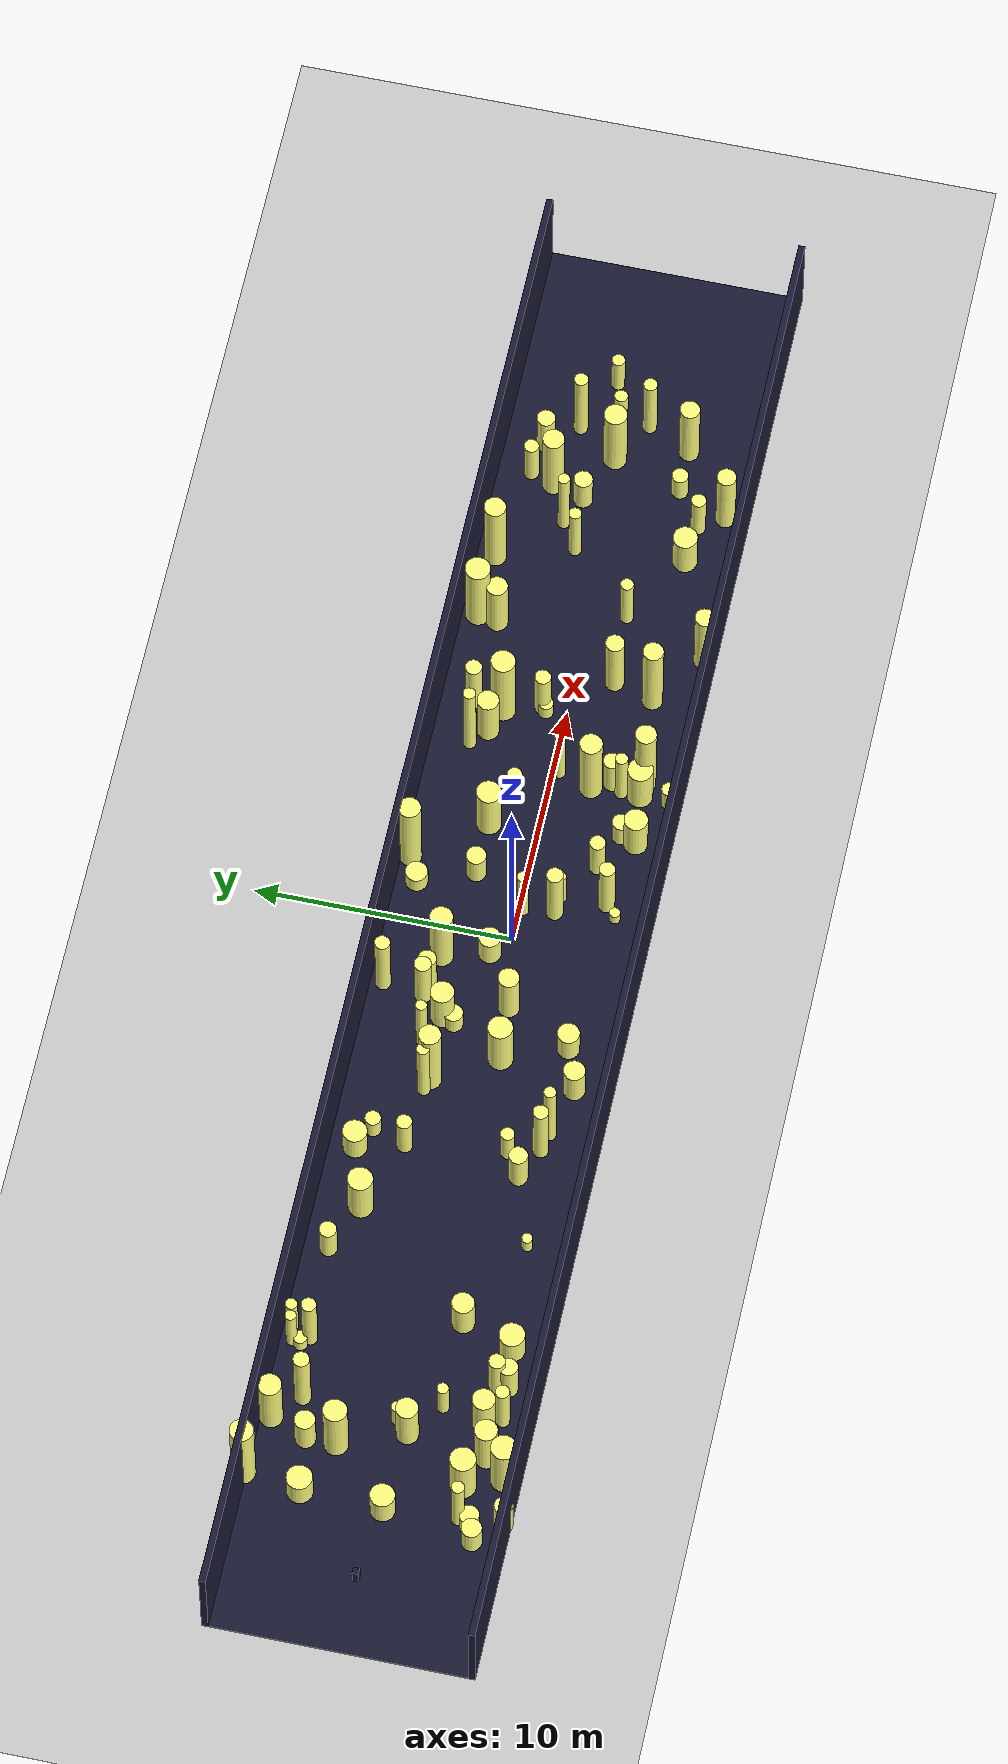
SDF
<?xml version="1.0"?>
<sdf version="1.4">
  <world name="default">
    <gui>
      <camera name="user_camera">
        <pose>-20 -30 40 0 0.66 0.83</pose>
      </camera>
    </gui>
    <include>
      <uri>model://ground_plane</uri>
    </include>
    <include>
      <uri>model://sun</uri>
    </include>
    <scene>
      <shadows>0</shadows>
    </scene>
    <model name="forest">
      <static>true</static>
      <link name="cylinder0">
        <pose>17.474350058050383 -3.0349304535474007 0.9654857216544241 0 0 0 </pose>
        <visual name="visual">
          <geometry>
            <cylinder>
              <radius>0.479023355841757</radius>
              <length>1.9309714433088483</length>
            </cylinder>
          </geometry>
          <material>
            <ambient>0.6 0.6 0.6 1</ambient>
            <diffuse>1 1 0.5 1</diffuse>
            <specular>0 0 0</specular>
            <emissive>0 0 0 1</emissive>
          </material>
        </visual>
        <collision name="collision">
          <geometry>
            <cylinder>
              <radius>0.479023355841757</radius>
              <length>1.9309714433088483</length>
            </cylinder>
          </geometry>
          <max_contacts>0</max_contacts>
        </collision>
      </link>
      <link name="cylinder1">
        <pose>4.981119732722934 -3.7257389631529083 1.0225231877695053 0 0 0 </pose>
        <visual name="visual">
          <geometry>
            <cylinder>
              <radius>0.4604490138018022</radius>
              <length>2.0450463755390107</length>
            </cylinder>
          </geometry>
          <material>
            <ambient>0.6 0.6 0.6 1</ambient>
            <diffuse>1 1 0.5 1</diffuse>
            <specular>0 0 0</specular>
            <emissive>0 0 0 1</emissive>
          </material>
        </visual>
        <collision name="collision">
          <geometry>
            <cylinder>
              <radius>0.4604490138018022</radius>
              <length>2.0450463755390107</length>
            </cylinder>
          </geometry>
          <max_contacts>0</max_contacts>
        </collision>
      </link>
      <link name="cylinder2">
        <pose>-5.754748853354975 -3.6356995572683193 0.8611136780357529 0 0 0 </pose>
        <visual name="visual">
          <geometry>
            <cylinder>
              <radius>0.417394056659338</radius>
              <length>1.7222273560715058</length>
            </cylinder>
          </geometry>
          <material>
            <ambient>0.6 0.6 0.6 1</ambient>
            <diffuse>1 1 0.5 1</diffuse>
            <specular>0 0 0</specular>
            <emissive>0 0 0 1</emissive>
          </material>
        </visual>
        <collision name="collision">
          <geometry>
            <cylinder>
              <radius>0.417394056659338</radius>
              <length>1.7222273560715058</length>
            </cylinder>
          </geometry>
          <max_contacts>0</max_contacts>
        </collision>
      </link>
      <link name="cylinder3">
        <pose>-22.554614542541916 -3.043304144231457 1.2346718837196298 0 0 0 </pose>
        <visual name="visual">
          <geometry>
            <cylinder>
              <radius>0.4905226006327724</radius>
              <length>2.4693437674392595</length>
            </cylinder>
          </geometry>
          <material>
            <ambient>0.6 0.6 0.6 1</ambient>
            <diffuse>1 1 0.5 1</diffuse>
            <specular>0 0 0</specular>
            <emissive>0 0 0 1</emissive>
          </material>
        </visual>
        <collision name="collision">
          <geometry>
            <cylinder>
              <radius>0.4905226006327724</radius>
              <length>2.4693437674392595</length>
            </cylinder>
          </geometry>
          <max_contacts>0</max_contacts>
        </collision>
      </link>
      <link name="cylinder4">
        <pose>22.26100889590525 -2.1995081622203716 1.6780744197933548 0 0 0 </pose>
        <visual name="visual">
          <geometry>
            <cylinder>
              <radius>0.3907151714520144</radius>
              <length>3.3561488395867096</length>
            </cylinder>
          </geometry>
          <material>
            <ambient>0.6 0.6 0.6 1</ambient>
            <diffuse>1 1 0.5 1</diffuse>
            <specular>0 0 0</specular>
            <emissive>0 0 0 1</emissive>
          </material>
        </visual>
        <collision name="collision">
          <geometry>
            <cylinder>
              <radius>0.3907151714520144</radius>
              <length>3.3561488395867096</length>
            </cylinder>
          </geometry>
          <max_contacts>0</max_contacts>
        </collision>
      </link>
      <link name="cylinder5">
        <pose>13.33595052830114 -4.642942753143084 1.7284169206716375 0 0 0 </pose>
        <visual name="visual">
          <geometry>
            <cylinder>
              <radius>0.3890159434390348</radius>
              <length>3.456833841343275</length>
            </cylinder>
          </geometry>
          <material>
            <ambient>0.6 0.6 0.6 1</ambient>
            <diffuse>1 1 0.5 1</diffuse>
            <specular>0 0 0</specular>
            <emissive>0 0 0 1</emissive>
          </material>
        </visual>
        <collision name="collision">
          <geometry>
            <cylinder>
              <radius>0.3890159434390348</radius>
              <length>3.456833841343275</length>
            </cylinder>
          </geometry>
          <max_contacts>0</max_contacts>
        </collision>
      </link>
      <link name="cylinder6">
        <pose>2.083699437350038 -1.4215035044701274 0.9485511643365495 0 0 0 </pose>
        <visual name="visual">
          <geometry>
            <cylinder>
              <radius>0.21684499694005663</radius>
              <length>1.897102328673099</length>
            </cylinder>
          </geometry>
          <material>
            <ambient>0.6 0.6 0.6 1</ambient>
            <diffuse>1 1 0.5 1</diffuse>
            <specular>0 0 0</specular>
            <emissive>0 0 0 1</emissive>
          </material>
        </visual>
        <collision name="collision">
          <geometry>
            <cylinder>
              <radius>0.21684499694005663</radius>
              <length>1.897102328673099</length>
            </cylinder>
          </geometry>
          <max_contacts>0</max_contacts>
        </collision>
      </link>
      <link name="cylinder7">
        <pose>9.601256511389927 2.424961302580276 1.960368952381102 0 0 0 </pose>
        <visual name="visual">
          <geometry>
            <cylinder>
              <radius>0.4792568903990782</radius>
              <length>3.920737904762204</length>
            </cylinder>
          </geometry>
          <material>
            <ambient>0.6 0.6 0.6 1</ambient>
            <diffuse>1 1 0.5 1</diffuse>
            <specular>0 0 0</specular>
            <emissive>0 0 0 1</emissive>
          </material>
        </visual>
        <collision name="collision">
          <geometry>
            <cylinder>
              <radius>0.4792568903990782</radius>
              <length>3.920737904762204</length>
            </cylinder>
          </geometry>
          <max_contacts>0</max_contacts>
        </collision>
      </link>
      <link name="cylinder8">
        <pose>9.742094447221689 3.6039482852947167 1.38029477843272 0 0 0 </pose>
        <visual name="visual">
          <geometry>
            <cylinder>
              <radius>0.32385085328464713</radius>
              <length>2.76058955686544</length>
            </cylinder>
          </geometry>
          <material>
            <ambient>0.6 0.6 0.6 1</ambient>
            <diffuse>1 1 0.5 1</diffuse>
            <specular>0 0 0</specular>
            <emissive>0 0 0 1</emissive>
          </material>
        </visual>
        <collision name="collision">
          <geometry>
            <cylinder>
              <radius>0.32385085328464713</radius>
              <length>2.76058955686544</length>
            </cylinder>
          </geometry>
          <max_contacts>0</max_contacts>
        </collision>
      </link>
      <link name="cylinder9">
        <pose>-23.904101613857705 -3.1530759208584644 1.4693353264752327 0 0 0 </pose>
        <visual name="visual">
          <geometry>
            <cylinder>
              <radius>0.24433035102363163</radius>
              <length>2.9386706529504654</length>
            </cylinder>
          </geometry>
          <material>
            <ambient>0.6 0.6 0.6 1</ambient>
            <diffuse>1 1 0.5 1</diffuse>
            <specular>0 0 0</specular>
            <emissive>0 0 0 1</emissive>
          </material>
        </visual>
        <collision name="collision">
          <geometry>
            <cylinder>
              <radius>0.24433035102363163</radius>
              <length>2.9386706529504654</length>
            </cylinder>
          </geometry>
          <max_contacts>0</max_contacts>
        </collision>
      </link>
      <link name="cylinder10">
        <pose>6.990896955859142 -1.551141580334158 1.794815221802227 0 0 0 </pose>
        <visual name="visual">
          <geometry>
            <cylinder>
              <radius>0.44472197589610934</radius>
              <length>3.589630443604454</length>
            </cylinder>
          </geometry>
          <material>
            <ambient>0.6 0.6 0.6 1</ambient>
            <diffuse>1 1 0.5 1</diffuse>
            <specular>0 0 0</specular>
            <emissive>0 0 0 1</emissive>
          </material>
        </visual>
        <collision name="collision">
          <geometry>
            <cylinder>
              <radius>0.44472197589610934</radius>
              <length>3.589630443604454</length>
            </cylinder>
          </geometry>
          <max_contacts>0</max_contacts>
        </collision>
      </link>
      <link name="cylinder11">
        <pose>-12.487149111359585 -3.2835647577086347 0.3931674047471566 0 0 0 </pose>
        <visual name="visual">
          <geometry>
            <cylinder>
              <radius>0.2045534972430673</radius>
              <length>0.7863348094943132</length>
            </cylinder>
          </geometry>
          <material>
            <ambient>0.6 0.6 0.6 1</ambient>
            <diffuse>1 1 0.5 1</diffuse>
            <specular>0 0 0</specular>
            <emissive>0 0 0 1</emissive>
          </material>
        </visual>
        <collision name="collision">
          <geometry>
            <cylinder>
              <radius>0.2045534972430673</radius>
              <length>0.7863348094943132</length>
            </cylinder>
          </geometry>
          <max_contacts>0</max_contacts>
        </collision>
      </link>
      <link name="cylinder12">
        <pose>-19.909525238158977 -3.2473207207106745 1.0920424826775004 0 0 0 </pose>
        <visual name="visual">
          <geometry>
            <cylinder>
              <radius>0.4372468424831488</radius>
              <length>2.1840849653550007</length>
            </cylinder>
          </geometry>
          <material>
            <ambient>0.6 0.6 0.6 1</ambient>
            <diffuse>1 1 0.5 1</diffuse>
            <specular>0 0 0</specular>
            <emissive>0 0 0 1</emissive>
          </material>
        </visual>
        <collision name="collision">
          <geometry>
            <cylinder>
              <radius>0.4372468424831488</radius>
              <length>2.1840849653550007</length>
            </cylinder>
          </geometry>
          <max_contacts>0</max_contacts>
        </collision>
      </link>
      <link name="cylinder13">
        <pose>-21.98805036154612 -4.456281456834889 1.4657374016018136 0 0 0 </pose>
        <visual name="visual">
          <geometry>
            <cylinder>
              <radius>0.49814442446754154</radius>
              <length>2.9314748032036273</length>
            </cylinder>
          </geometry>
          <material>
            <ambient>0.6 0.6 0.6 1</ambient>
            <diffuse>1 1 0.5 1</diffuse>
            <specular>0 0 0</specular>
            <emissive>0 0 0 1</emissive>
          </material>
        </visual>
        <collision name="collision">
          <geometry>
            <cylinder>
              <radius>0.49814442446754154</radius>
              <length>2.9314748032036273</length>
            </cylinder>
          </geometry>
          <max_contacts>0</max_contacts>
        </collision>
      </link>
      <link name="cylinder14">
        <pose>-21.308032298656737 4.495210251003124 1.4383848407434416 0 0 0 </pose>
        <visual name="visual">
          <geometry>
            <cylinder>
              <radius>0.4465633740316827</radius>
              <length>2.8767696814868833</length>
            </cylinder>
          </geometry>
          <material>
            <ambient>0.6 0.6 0.6 1</ambient>
            <diffuse>1 1 0.5 1</diffuse>
            <specular>0 0 0</specular>
            <emissive>0 0 0 1</emissive>
          </material>
        </visual>
        <collision name="collision">
          <geometry>
            <cylinder>
              <radius>0.4465633740316827</radius>
              <length>2.8767696814868833</length>
            </cylinder>
          </geometry>
          <max_contacts>0</max_contacts>
        </collision>
      </link>
      <link name="cylinder15">
        <pose>13.340676952182172 3.4753915415929235 1.4218001322765699 0 0 0 </pose>
        <visual name="visual">
          <geometry>
            <cylinder>
              <radius>0.4169326418490212</radius>
              <length>2.8436002645531397</length>
            </cylinder>
          </geometry>
          <material>
            <ambient>0.6 0.6 0.6 1</ambient>
            <diffuse>1 1 0.5 1</diffuse>
            <specular>0 0 0</specular>
            <emissive>0 0 0 1</emissive>
          </material>
        </visual>
        <collision name="collision">
          <geometry>
            <cylinder>
              <radius>0.4169326418490212</radius>
              <length>2.8436002645531397</length>
            </cylinder>
          </geometry>
          <max_contacts>0</max_contacts>
        </collision>
      </link>
      <link name="cylinder16">
        <pose>-9.798764212053829 3.8855375509682233 0.7028864098086872 0 0 0 </pose>
        <visual name="visual">
          <geometry>
            <cylinder>
              <radius>0.46580999178694366</radius>
              <length>1.4057728196173744</length>
            </cylinder>
          </geometry>
          <material>
            <ambient>0.6 0.6 0.6 1</ambient>
            <diffuse>1 1 0.5 1</diffuse>
            <specular>0 0 0</specular>
            <emissive>0 0 0 1</emissive>
          </material>
        </visual>
        <collision name="collision">
          <geometry>
            <cylinder>
              <radius>0.46580999178694366</radius>
              <length>1.4057728196173744</length>
            </cylinder>
          </geometry>
          <max_contacts>0</max_contacts>
        </collision>
      </link>
      <link name="cylinder17">
        <pose>-24.08733993064421 -3.6108653907759747 0.5645090989712589 0 0 0 </pose>
        <visual name="visual">
          <geometry>
            <cylinder>
              <radius>0.37873455461479266</radius>
              <length>1.1290181979425178</length>
            </cylinder>
          </geometry>
          <material>
            <ambient>0.6 0.6 0.6 1</ambient>
            <diffuse>1 1 0.5 1</diffuse>
            <specular>0 0 0</specular>
            <emissive>0 0 0 1</emissive>
          </material>
        </visual>
        <collision name="collision">
          <geometry>
            <cylinder>
              <radius>0.37873455461479266</radius>
              <length>1.1290181979425178</length>
            </cylinder>
          </geometry>
          <max_contacts>0</max_contacts>
        </collision>
      </link>
      <link name="cylinder18">
        <pose>-2.8648793312948158 -0.4965705589481839 1.2666190422965533 0 0 0 </pose>
        <visual name="visual">
          <geometry>
            <cylinder>
              <radius>0.4087606420837506</radius>
              <length>2.5332380845931066</length>
            </cylinder>
          </geometry>
          <material>
            <ambient>0.6 0.6 0.6 1</ambient>
            <diffuse>1 1 0.5 1</diffuse>
            <specular>0 0 0</specular>
            <emissive>0 0 0 1</emissive>
          </material>
        </visual>
        <collision name="collision">
          <geometry>
            <cylinder>
              <radius>0.4087606420837506</radius>
              <length>2.5332380845931066</length>
            </cylinder>
          </geometry>
          <max_contacts>0</max_contacts>
        </collision>
      </link>
      <link name="cylinder19">
        <pose>-24.025993534648727 2.785799897097611 0.6539868889832356 0 0 0 </pose>
        <visual name="visual">
          <geometry>
            <cylinder>
              <radius>0.4966410289199009</radius>
              <length>1.3079737779664713</length>
            </cylinder>
          </geometry>
          <material>
            <ambient>0.6 0.6 0.6 1</ambient>
            <diffuse>1 1 0.5 1</diffuse>
            <specular>0 0 0</specular>
            <emissive>0 0 0 1</emissive>
          </material>
        </visual>
        <collision name="collision">
          <geometry>
            <cylinder>
              <radius>0.4966410289199009</radius>
              <length>1.3079737779664713</length>
            </cylinder>
          </geometry>
          <max_contacts>0</max_contacts>
        </collision>
      </link>
      <link name="cylinder20">
        <pose>19.034700898979835 -3.231470783861803 1.0958777769155494 0 0 0 </pose>
        <visual name="visual">
          <geometry>
            <cylinder>
              <radius>0.2891964671625721</radius>
              <length>2.191755553831099</length>
            </cylinder>
          </geometry>
          <material>
            <ambient>0.6 0.6 0.6 1</ambient>
            <diffuse>1 1 0.5 1</diffuse>
            <specular>0 0 0</specular>
            <emissive>0 0 0 1</emissive>
          </material>
        </visual>
        <collision name="collision">
          <geometry>
            <cylinder>
              <radius>0.2891964671625721</radius>
              <length>2.191755553831099</length>
            </cylinder>
          </geometry>
          <max_contacts>0</max_contacts>
        </collision>
      </link>
      <link name="cylinder21">
        <pose>19.74069789002226 2.639889300821311 1.7884892320661283 0 0 0 </pose>
        <visual name="visual">
          <geometry>
            <cylinder>
              <radius>0.4281758525312108</radius>
              <length>3.5769784641322566</length>
            </cylinder>
          </geometry>
          <material>
            <ambient>0.6 0.6 0.6 1</ambient>
            <diffuse>1 1 0.5 1</diffuse>
            <specular>0 0 0</specular>
            <emissive>0 0 0 1</emissive>
          </material>
        </visual>
        <collision name="collision">
          <geometry>
            <cylinder>
              <radius>0.4281758525312108</radius>
              <length>3.5769784641322566</length>
            </cylinder>
          </geometry>
          <max_contacts>0</max_contacts>
        </collision>
      </link>
      <link name="cylinder22">
        <pose>10.028819131293751 0.9667783642480341 1.242532234555234 0 0 0 </pose>
        <visual name="visual">
          <geometry>
            <cylinder>
              <radius>0.3125013418587146</radius>
              <length>2.485064469110468</length>
            </cylinder>
          </geometry>
          <material>
            <ambient>0.6 0.6 0.6 1</ambient>
            <diffuse>1 1 0.5 1</diffuse>
            <specular>0 0 0</specular>
            <emissive>0 0 0 1</emissive>
          </material>
        </visual>
        <collision name="collision">
          <geometry>
            <cylinder>
              <radius>0.3125013418587146</radius>
              <length>2.485064469110468</length>
            </cylinder>
          </geometry>
          <max_contacts>0</max_contacts>
        </collision>
      </link>
      <link name="cylinder23">
        <pose>-23.755383899373843 -4.822070672983206 0.8719483692005128 0 0 0 </pose>
        <visual name="visual">
          <geometry>
            <cylinder>
              <radius>0.3529152888837135</radius>
              <length>1.7438967384010255</length>
            </cylinder>
          </geometry>
          <material>
            <ambient>0.6 0.6 0.6 1</ambient>
            <diffuse>1 1 0.5 1</diffuse>
            <specular>0 0 0</specular>
            <emissive>0 0 0 1</emissive>
          </material>
        </visual>
        <collision name="collision">
          <geometry>
            <cylinder>
              <radius>0.3529152888837135</radius>
              <length>1.7438967384010255</length>
            </cylinder>
          </geometry>
          <max_contacts>0</max_contacts>
        </collision>
      </link>
      <link name="cylinder24">
        <pose>21.432369416347754 3.2905600152771974 1.0591906268662163 0 0 0 </pose>
        <visual name="visual">
          <geometry>
            <cylinder>
              <radius>0.36264364448251285</radius>
              <length>2.1183812537324327</length>
            </cylinder>
          </geometry>
          <material>
            <ambient>0.6 0.6 0.6 1</ambient>
            <diffuse>1 1 0.5 1</diffuse>
            <specular>0 0 0</specular>
            <emissive>0 0 0 1</emissive>
          </material>
        </visual>
        <collision name="collision">
          <geometry>
            <cylinder>
              <radius>0.36264364448251285</radius>
              <length>2.1183812537324327</length>
            </cylinder>
          </geometry>
          <max_contacts>0</max_contacts>
        </collision>
      </link>
      <link name="cylinder25">
        <pose>-16.065959980252472 -1.6298136352520673 0.9016604387363361 0 0 0 </pose>
        <visual name="visual">
          <geometry>
            <cylinder>
              <radius>0.4349925042361094</radius>
              <length>1.8033208774726721</length>
            </cylinder>
          </geometry>
          <material>
            <ambient>0.6 0.6 0.6 1</ambient>
            <diffuse>1 1 0.5 1</diffuse>
            <specular>0 0 0</specular>
            <emissive>0 0 0 1</emissive>
          </material>
        </visual>
        <collision name="collision">
          <geometry>
            <cylinder>
              <radius>0.4349925042361094</radius>
              <length>1.8033208774726721</length>
            </cylinder>
          </geometry>
          <max_contacts>0</max_contacts>
        </collision>
      </link>
      <link name="cylinder26">
        <pose>-6.442579740546456 1.7434035630056837 1.8863791940662549 0 0 0 </pose>
        <visual name="visual">
          <geometry>
            <cylinder>
              <radius>0.42650104526686883</radius>
              <length>3.7727583881325097</length>
            </cylinder>
          </geometry>
          <material>
            <ambient>0.6 0.6 0.6 1</ambient>
            <diffuse>1 1 0.5 1</diffuse>
            <specular>0 0 0</specular>
            <emissive>0 0 0 1</emissive>
          </material>
        </visual>
        <collision name="collision">
          <geometry>
            <cylinder>
              <radius>0.42650104526686883</radius>
              <length>3.7727583881325097</length>
            </cylinder>
          </geometry>
          <max_contacts>0</max_contacts>
        </collision>
      </link>
      <link name="cylinder27">
        <pose>5.173194019723276 -3.116572948917123 0.6256688202765066 0 0 0 </pose>
        <visual name="visual">
          <geometry>
            <cylinder>
              <radius>0.34411350651951184</radius>
              <length>1.2513376405530132</length>
            </cylinder>
          </geometry>
          <material>
            <ambient>0.6 0.6 0.6 1</ambient>
            <diffuse>1 1 0.5 1</diffuse>
            <specular>0 0 0</specular>
            <emissive>0 0 0 1</emissive>
          </material>
        </visual>
        <collision name="collision">
          <geometry>
            <cylinder>
              <radius>0.34411350651951184</radius>
              <length>1.2513376405530132</length>
            </cylinder>
          </geometry>
          <max_contacts>0</max_contacts>
        </collision>
      </link>
      <link name="cylinder28">
        <pose>-21.263672964767206 -3.6311780743026945 1.2680707339227801 0 0 0 </pose>
        <visual name="visual">
          <geometry>
            <cylinder>
              <radius>0.4388341553206505</radius>
              <length>2.5361414678455603</length>
            </cylinder>
          </geometry>
          <material>
            <ambient>0.6 0.6 0.6 1</ambient>
            <diffuse>1 1 0.5 1</diffuse>
            <specular>0 0 0</specular>
            <emissive>0 0 0 1</emissive>
          </material>
        </visual>
        <collision name="collision">
          <geometry>
            <cylinder>
              <radius>0.4388341553206505</radius>
              <length>2.5361414678455603</length>
            </cylinder>
          </geometry>
          <max_contacts>0</max_contacts>
        </collision>
      </link>
      <link name="cylinder29">
        <pose>-14.127295966950221 3.935134634446454 0.853269335998126 0 0 0 </pose>
        <visual name="visual">
          <geometry>
            <cylinder>
              <radius>0.33078512619020045</radius>
              <length>1.706538671996252</length>
            </cylinder>
          </geometry>
          <material>
            <ambient>0.6 0.6 0.6 1</ambient>
            <diffuse>1 1 0.5 1</diffuse>
            <specular>0 0 0</specular>
            <emissive>0 0 0 1</emissive>
          </material>
        </visual>
        <collision name="collision">
          <geometry>
            <cylinder>
              <radius>0.33078512619020045</radius>
              <length>1.706538671996252</length>
            </cylinder>
          </geometry>
          <max_contacts>0</max_contacts>
        </collision>
      </link>
      <link name="cylinder30">
        <pose>16.150703960999316 4.161689183484395 1.9443778139249177 0 0 0 </pose>
        <visual name="visual">
          <geometry>
            <cylinder>
              <radius>0.4260707346098702</radius>
              <length>3.8887556278498354</length>
            </cylinder>
          </geometry>
          <material>
            <ambient>0.6 0.6 0.6 1</ambient>
            <diffuse>1 1 0.5 1</diffuse>
            <specular>0 0 0</specular>
            <emissive>0 0 0 1</emissive>
          </material>
        </visual>
        <collision name="collision">
          <geometry>
            <cylinder>
              <radius>0.4260707346098702</radius>
              <length>3.8887556278498354</length>
            </cylinder>
          </geometry>
          <max_contacts>0</max_contacts>
        </collision>
      </link>
      <link name="cylinder31">
        <pose>20.468062265337892 -2.2148263954350336 0.6623111697631872 0 0 0 </pose>
        <visual name="visual">
          <geometry>
            <cylinder>
              <radius>0.3240726301415455</radius>
              <length>1.3246223395263743</length>
            </cylinder>
          </geometry>
          <material>
            <ambient>0.6 0.6 0.6 1</ambient>
            <diffuse>1 1 0.5 1</diffuse>
            <specular>0 0 0</specular>
            <emissive>0 0 0 1</emissive>
          </material>
        </visual>
        <collision name="collision">
          <geometry>
            <cylinder>
              <radius>0.3240726301415455</radius>
              <length>1.3246223395263743</length>
            </cylinder>
          </geometry>
          <max_contacts>0</max_contacts>
        </collision>
      </link>
      <link name="cylinder32">
        <pose>1.680699917737826 -3.6193126956154478 0.29244209586093084 0 0 0 </pose>
        <visual name="visual">
          <geometry>
            <cylinder>
              <radius>0.2092950892574559</radius>
              <length>0.5848841917218617</length>
            </cylinder>
          </geometry>
          <material>
            <ambient>0.6 0.6 0.6 1</ambient>
            <diffuse>1 1 0.5 1</diffuse>
            <specular>0 0 0</specular>
            <emissive>0 0 0 1</emissive>
          </material>
        </visual>
        <collision name="collision">
          <geometry>
            <cylinder>
              <radius>0.2092950892574559</radius>
              <length>0.5848841917218617</length>
            </cylinder>
          </geometry>
          <max_contacts>0</max_contacts>
        </collision>
      </link>
      <link name="cylinder33">
        <pose>9.863504967454482 0.808594310656428 0.3964918212273452 0 0 0 </pose>
        <visual name="visual">
          <geometry>
            <cylinder>
              <radius>0.2902772387612938</radius>
              <length>0.7929836424546904</length>
            </cylinder>
          </geometry>
          <material>
            <ambient>0.6 0.6 0.6 1</ambient>
            <diffuse>1 1 0.5 1</diffuse>
            <specular>0 0 0</specular>
            <emissive>0 0 0 1</emissive>
          </material>
        </visual>
        <collision name="collision">
          <geometry>
            <cylinder>
              <radius>0.2902772387612938</radius>
              <length>0.7929836424546904</length>
            </cylinder>
          </geometry>
          <max_contacts>0</max_contacts>
        </collision>
      </link>
      <link name="cylinder34">
        <pose>-3.7671409269096117 1.8649424314652832 1.054442484710619 0 0 0 </pose>
        <visual name="visual">
          <geometry>
            <cylinder>
              <radius>0.46116832143360736</radius>
              <length>2.108884969421238</length>
            </cylinder>
          </geometry>
          <material>
            <ambient>0.6 0.6 0.6 1</ambient>
            <diffuse>1 1 0.5 1</diffuse>
            <specular>0 0 0</specular>
            <emissive>0 0 0 1</emissive>
          </material>
        </visual>
        <collision name="collision">
          <geometry>
            <cylinder>
              <radius>0.46116832143360736</radius>
              <length>2.108884969421238</length>
            </cylinder>
          </geometry>
          <max_contacts>0</max_contacts>
        </collision>
      </link>
      <link name="cylinder35">
        <pose>-0.7602056430930197 0.693844699559337 0.7039703608118021 0 0 0 </pose>
        <visual name="visual">
          <geometry>
            <cylinder>
              <radius>0.43070909559110426</radius>
              <length>1.4079407216236042</length>
            </cylinder>
          </geometry>
          <material>
            <ambient>0.6 0.6 0.6 1</ambient>
            <diffuse>1 1 0.5 1</diffuse>
            <specular>0 0 0</specular>
            <emissive>0 0 0 1</emissive>
          </material>
        </visual>
        <collision name="collision">
          <geometry>
            <cylinder>
              <radius>0.43070909559110426</radius>
              <length>1.4079407216236042</length>
            </cylinder>
          </geometry>
          <max_contacts>0</max_contacts>
        </collision>
      </link>
      <link name="cylinder36">
        <pose>7.3627164502554265 -0.2668266840622504 1.5181494502579536 0 0 0 </pose>
        <visual name="visual">
          <geometry>
            <cylinder>
              <radius>0.2097716151069922</radius>
              <length>3.036298900515907</length>
            </cylinder>
          </geometry>
          <material>
            <ambient>0.6 0.6 0.6 1</ambient>
            <diffuse>1 1 0.5 1</diffuse>
            <specular>0 0 0</specular>
            <emissive>0 0 0 1</emissive>
          </material>
        </visual>
        <collision name="collision">
          <geometry>
            <cylinder>
              <radius>0.2097716151069922</radius>
              <length>3.036298900515907</length>
            </cylinder>
          </geometry>
          <max_contacts>0</max_contacts>
        </collision>
      </link>
      <link name="cylinder37">
        <pose>-4.921027424248525 2.4121538878717725 1.5081504087877833 0 0 0 </pose>
        <visual name="visual">
          <geometry>
            <cylinder>
              <radius>0.21834722863311687</radius>
              <length>3.0163008175755666</length>
            </cylinder>
          </geometry>
          <material>
            <ambient>0.6 0.6 0.6 1</ambient>
            <diffuse>1 1 0.5 1</diffuse>
            <specular>0 0 0</specular>
            <emissive>0 0 0 1</emissive>
          </material>
        </visual>
        <collision name="collision">
          <geometry>
            <cylinder>
              <radius>0.21834722863311687</radius>
              <length>3.0163008175755666</length>
            </cylinder>
          </geometry>
          <max_contacts>0</max_contacts>
        </collision>
      </link>
      <link name="cylinder38">
        <pose>23.05829503605309 -0.4798861230173177 1.6580908223486408 0 0 0 </pose>
        <visual name="visual">
          <geometry>
            <cylinder>
              <radius>0.2744843459543446</radius>
              <length>3.3161816446972816</length>
            </cylinder>
          </geometry>
          <material>
            <ambient>0.6 0.6 0.6 1</ambient>
            <diffuse>1 1 0.5 1</diffuse>
            <specular>0 0 0</specular>
            <emissive>0 0 0 1</emissive>
          </material>
        </visual>
        <collision name="collision">
          <geometry>
            <cylinder>
              <radius>0.2744843459543446</radius>
              <length>3.3161816446972816</length>
            </cylinder>
          </geometry>
          <max_contacts>0</max_contacts>
        </collision>
      </link>
      <link name="cylinder39">
        <pose>-20.93103883253957 -0.5839638680604544 1.1809114135723586 0 0 0 </pose>
        <visual name="visual">
          <geometry>
            <cylinder>
              <radius>0.42660397344079437</radius>
              <length>2.3618228271447173</length>
            </cylinder>
          </geometry>
          <material>
            <ambient>0.6 0.6 0.6 1</ambient>
            <diffuse>1 1 0.5 1</diffuse>
            <specular>0 0 0</specular>
            <emissive>0 0 0 1</emissive>
          </material>
        </visual>
        <collision name="collision">
          <geometry>
            <cylinder>
              <radius>0.42660397344079437</radius>
              <length>2.3618228271447173</length>
            </cylinder>
          </geometry>
          <max_contacts>0</max_contacts>
        </collision>
      </link>
      <link name="cylinder40">
        <pose>1.3012875947699953 -0.13856883436392842 1.3926023500930211 0 0 0 </pose>
        <visual name="visual">
          <geometry>
            <cylinder>
              <radius>0.2205407637531081</radius>
              <length>2.7852047001860423</length>
            </cylinder>
          </geometry>
          <material>
            <ambient>0.6 0.6 0.6 1</ambient>
            <diffuse>1 1 0.5 1</diffuse>
            <specular>0 0 0</specular>
            <emissive>0 0 0 1</emissive>
          </material>
        </visual>
        <collision name="collision">
          <geometry>
            <cylinder>
              <radius>0.2205407637531081</radius>
              <length>2.7852047001860423</length>
            </cylinder>
          </geometry>
          <max_contacts>0</max_contacts>
        </collision>
      </link>
      <link name="cylinder41">
        <pose>7.368683766399791 -2.2983883685452575 0.9258939166206205 0 0 0 </pose>
        <visual name="visual">
          <geometry>
            <cylinder>
              <radius>0.34303641036955945</radius>
              <length>1.851787833241241</length>
            </cylinder>
          </geometry>
          <material>
            <ambient>0.6 0.6 0.6 1</ambient>
            <diffuse>1 1 0.5 1</diffuse>
            <specular>0 0 0</specular>
            <emissive>0 0 0 1</emissive>
          </material>
        </visual>
        <collision name="collision">
          <geometry>
            <cylinder>
              <radius>0.34303641036955945</radius>
              <length>1.851787833241241</length>
            </cylinder>
          </geometry>
          <max_contacts>0</max_contacts>
        </collision>
      </link>
      <link name="cylinder42">
        <pose>-20.3046763870438 3.518755402546116 1.7072282281849482 0 0 0 </pose>
        <visual name="visual">
          <geometry>
            <cylinder>
              <radius>0.31130974515695226</radius>
              <length>3.4144564563698965</length>
            </cylinder>
          </geometry>
          <material>
            <ambient>0.6 0.6 0.6 1</ambient>
            <diffuse>1 1 0.5 1</diffuse>
            <specular>0 0 0</specular>
            <emissive>0 0 0 1</emissive>
          </material>
        </visual>
        <collision name="collision">
          <geometry>
            <cylinder>
              <radius>0.31130974515695226</radius>
              <length>3.4144564563698965</length>
            </cylinder>
          </geometry>
          <max_contacts>0</max_contacts>
        </collision>
      </link>
      <link name="cylinder43">
        <pose>-3.960138168719922 1.3981410458650423 0.4783969110256533 0 0 0 </pose>
        <visual name="visual">
          <geometry>
            <cylinder>
              <radius>0.36497700427004953</radius>
              <length>0.9567938220513066</length>
            </cylinder>
          </geometry>
          <material>
            <ambient>0.6 0.6 0.6 1</ambient>
            <diffuse>1 1 0.5 1</diffuse>
            <specular>0 0 0</specular>
            <emissive>0 0 0 1</emissive>
          </material>
        </visual>
        <collision name="collision">
          <geometry>
            <cylinder>
              <radius>0.36497700427004953</radius>
              <length>0.9567938220513066</length>
            </cylinder>
          </geometry>
          <max_contacts>0</max_contacts>
        </collision>
      </link>
      <link name="cylinder44">
        <pose>-9.354849034871032 2.0879329908388575 1.0376829949513398 0 0 0 </pose>
        <visual name="visual">
          <geometry>
            <cylinder>
              <radius>0.2981524959668884</radius>
              <length>2.0753659899026795</length>
            </cylinder>
          </geometry>
          <material>
            <ambient>0.6 0.6 0.6 1</ambient>
            <diffuse>1 1 0.5 1</diffuse>
            <specular>0 0 0</specular>
            <emissive>0 0 0 1</emissive>
          </material>
        </visual>
        <collision name="collision">
          <geometry>
            <cylinder>
              <radius>0.2981524959668884</radius>
              <length>2.0753659899026795</length>
            </cylinder>
          </geometry>
          <max_contacts>0</max_contacts>
        </collision>
      </link>
      <link name="cylinder45">
        <pose>-6.920800251284909 1.900744533748453 1.7276016508489844 0 0 0 </pose>
        <visual name="visual">
          <geometry>
            <cylinder>
              <radius>0.24138930201298717</radius>
              <length>3.455203301697969</length>
            </cylinder>
          </geometry>
          <material>
            <ambient>0.6 0.6 0.6 1</ambient>
            <diffuse>1 1 0.5 1</diffuse>
            <specular>0 0 0</specular>
            <emissive>0 0 0 1</emissive>
          </material>
        </visual>
        <collision name="collision">
          <geometry>
            <cylinder>
              <radius>0.24138930201298717</radius>
              <length>3.455203301697969</length>
            </cylinder>
          </geometry>
          <max_contacts>0</max_contacts>
        </collision>
      </link>
      <link name="cylinder46">
        <pose>11.668276562263593 -1.489181927137647 1.595949690401096 0 0 0 </pose>
        <visual name="visual">
          <geometry>
            <cylinder>
              <radius>0.36794035113910684</radius>
              <length>3.191899380802192</length>
            </cylinder>
          </geometry>
          <material>
            <ambient>0.6 0.6 0.6 1</ambient>
            <diffuse>1 1 0.5 1</diffuse>
            <specular>0 0 0</specular>
            <emissive>0 0 0 1</emissive>
          </material>
        </visual>
        <collision name="collision">
          <geometry>
            <cylinder>
              <radius>0.36794035113910684</radius>
              <length>3.191899380802192</length>
            </cylinder>
          </geometry>
          <max_contacts>0</max_contacts>
        </collision>
      </link>
      <link name="cylinder47">
        <pose>11.20340025141465 -3.0679908835565084 1.9767067778364764 0 0 0 </pose>
        <visual name="visual">
          <geometry>
            <cylinder>
              <radius>0.3995136676813486</radius>
              <length>3.953413555672953</length>
            </cylinder>
          </geometry>
          <material>
            <ambient>0.6 0.6 0.6 1</ambient>
            <diffuse>1 1 0.5 1</diffuse>
            <specular>0 0 0</specular>
            <emissive>0 0 0 1</emissive>
          </material>
        </visual>
        <collision name="collision">
          <geometry>
            <cylinder>
              <radius>0.3995136676813486</radius>
              <length>3.953413555672953</length>
            </cylinder>
          </geometry>
          <max_contacts>0</max_contacts>
        </collision>
      </link>
      <link name="cylinder48">
        <pose>1.6647512046453308 4.063980111714518 0.4371183833766389 0 0 0 </pose>
        <visual name="visual">
          <geometry>
            <cylinder>
              <radius>0.4283587279921878</radius>
              <length>0.8742367667532778</length>
            </cylinder>
          </geometry>
          <material>
            <ambient>0.6 0.6 0.6 1</ambient>
            <diffuse>1 1 0.5 1</diffuse>
            <specular>0 0 0</specular>
            <emissive>0 0 0 1</emissive>
          </material>
        </visual>
        <collision name="collision">
          <geometry>
            <cylinder>
              <radius>0.4283587279921878</radius>
              <length>0.8742367667532778</length>
            </cylinder>
          </geometry>
          <max_contacts>0</max_contacts>
        </collision>
      </link>
      <link name="cylinder49">
        <pose>-18.1016221116858 4.441922086407754 1.1128271327998167 0 0 0 </pose>
        <visual name="visual">
          <geometry>
            <cylinder>
              <radius>0.20882252836478943</radius>
              <length>2.2256542655996334</length>
            </cylinder>
          </geometry>
          <material>
            <ambient>0.6 0.6 0.6 1</ambient>
            <diffuse>1 1 0.5 1</diffuse>
            <specular>0 0 0</specular>
            <emissive>0 0 0 1</emissive>
          </material>
        </visual>
        <collision name="collision">
          <geometry>
            <cylinder>
              <radius>0.20882252836478943</radius>
              <length>2.2256542655996334</length>
            </cylinder>
          </geometry>
          <max_contacts>0</max_contacts>
        </collision>
      </link>
      <link name="cylinder50">
        <pose>2.667249374632725 4.529174650250976 1.9906787980647265 0 0 0 </pose>
        <visual name="visual">
          <geometry>
            <cylinder>
              <radius>0.4340732099337412</radius>
              <length>3.981357596129453</length>
            </cylinder>
          </geometry>
          <material>
            <ambient>0.6 0.6 0.6 1</ambient>
            <diffuse>1 1 0.5 1</diffuse>
            <specular>0 0 0</specular>
            <emissive>0 0 0 1</emissive>
          </material>
        </visual>
        <collision name="collision">
          <geometry>
            <cylinder>
              <radius>0.4340732099337412</radius>
              <length>3.981357596129453</length>
            </cylinder>
          </geometry>
          <max_contacts>0</max_contacts>
        </collision>
      </link>
      <link name="cylinder51">
        <pose>-9.748749280002844 -2.35167360003644 0.9599845280778108 0 0 0 </pose>
        <visual name="visual">
          <geometry>
            <cylinder>
              <radius>0.3630535850719547</radius>
              <length>1.9199690561556215</length>
            </cylinder>
          </geometry>
          <material>
            <ambient>0.6 0.6 0.6 1</ambient>
            <diffuse>1 1 0.5 1</diffuse>
            <specular>0 0 0</specular>
            <emissive>0 0 0 1</emissive>
          </material>
        </visual>
        <collision name="collision">
          <geometry>
            <cylinder>
              <radius>0.3630535850719547</radius>
              <length>1.9199690561556215</length>
            </cylinder>
          </geometry>
          <max_contacts>0</max_contacts>
        </collision>
      </link>
      <link name="cylinder52">
        <pose>-8.49063309788512 -2.934319017824949 1.6559985217201434 0 0 0 </pose>
        <visual name="visual">
          <geometry>
            <cylinder>
              <radius>0.2960132461056362</radius>
              <length>3.311997043440287</length>
            </cylinder>
          </geometry>
          <material>
            <ambient>0.6 0.6 0.6 1</ambient>
            <diffuse>1 1 0.5 1</diffuse>
            <specular>0 0 0</specular>
            <emissive>0 0 0 1</emissive>
          </material>
        </visual>
        <collision name="collision">
          <geometry>
            <cylinder>
              <radius>0.2960132461056362</radius>
              <length>3.311997043440287</length>
            </cylinder>
          </geometry>
          <max_contacts>0</max_contacts>
        </collision>
      </link>
      <link name="cylinder53">
        <pose>18.1401531018184 1.8894457020072286 1.7576686166153417 0 0 0 </pose>
        <visual name="visual">
          <geometry>
            <cylinder>
              <radius>0.22812469044872064</radius>
              <length>3.5153372332306834</length>
            </cylinder>
          </geometry>
          <material>
            <ambient>0.6 0.6 0.6 1</ambient>
            <diffuse>1 1 0.5 1</diffuse>
            <specular>0 0 0</specular>
            <emissive>0 0 0 1</emissive>
          </material>
        </visual>
        <collision name="collision">
          <geometry>
            <cylinder>
              <radius>0.22812469044872064</radius>
              <length>3.5153372332306834</length>
            </cylinder>
          </geometry>
          <max_contacts>0</max_contacts>
        </collision>
      </link>
      <link name="cylinder54">
        <pose>14.572585931318628 -1.3522918783037055 1.3345853702635546 0 0 0 </pose>
        <visual name="visual">
          <geometry>
            <cylinder>
              <radius>0.25575965259684974</radius>
              <length>2.6691707405271092</length>
            </cylinder>
          </geometry>
          <material>
            <ambient>0.6 0.6 0.6 1</ambient>
            <diffuse>1 1 0.5 1</diffuse>
            <specular>0 0 0</specular>
            <emissive>0 0 0 1</emissive>
          </material>
        </visual>
        <collision name="collision">
          <geometry>
            <cylinder>
              <radius>0.25575965259684974</radius>
              <length>2.6691707405271092</length>
            </cylinder>
          </geometry>
          <max_contacts>0</max_contacts>
        </collision>
      </link>
      <link name="cylinder55">
        <pose>3.698094316217322 -2.5134255271013553 1.0294614972973575 0 0 0 </pose>
        <visual name="visual">
          <geometry>
            <cylinder>
              <radius>0.3095883364873114</radius>
              <length>2.058922994594715</length>
            </cylinder>
          </geometry>
          <material>
            <ambient>0.6 0.6 0.6 1</ambient>
            <diffuse>1 1 0.5 1</diffuse>
            <specular>0 0 0</specular>
            <emissive>0 0 0 1</emissive>
          </material>
        </visual>
        <collision name="collision">
          <geometry>
            <cylinder>
              <radius>0.3095883364873114</radius>
              <length>2.058922994594715</length>
            </cylinder>
          </geometry>
          <max_contacts>0</max_contacts>
        </collision>
      </link>
      <link name="cylinder56">
        <pose>-8.938486943101697 3.388996790357263 0.505727104320048 0 0 0 </pose>
        <visual name="visual">
          <geometry>
            <cylinder>
              <radius>0.30769054493596926</radius>
              <length>1.011454208640096</length>
            </cylinder>
          </geometry>
          <material>
            <ambient>0.6 0.6 0.6 1</ambient>
            <diffuse>1 1 0.5 1</diffuse>
            <specular>0 0 0</specular>
            <emissive>0 0 0 1</emissive>
          </material>
        </visual>
        <collision name="collision">
          <geometry>
            <cylinder>
              <radius>0.30769054493596926</radius>
              <length>1.011454208640096</length>
            </cylinder>
          </geometry>
          <max_contacts>0</max_contacts>
        </collision>
      </link>
      <link name="cylinder57">
        <pose>-18.331109688945347 -3.8390072303231526 0.9790099665448058 0 0 0 </pose>
        <visual name="visual">
          <geometry>
            <cylinder>
              <radius>0.35577886355971566</radius>
              <length>1.9580199330896115</length>
            </cylinder>
          </geometry>
          <material>
            <ambient>0.6 0.6 0.6 1</ambient>
            <diffuse>1 1 0.5 1</diffuse>
            <specular>0 0 0</specular>
            <emissive>0 0 0 1</emissive>
          </material>
        </visual>
        <collision name="collision">
          <geometry>
            <cylinder>
              <radius>0.35577886355971566</radius>
              <length>1.9580199330896115</length>
            </cylinder>
          </geometry>
          <max_contacts>0</max_contacts>
        </collision>
      </link>
      <link name="cylinder58">
        <pose>-21.896229772252173 1.8964191180577306 1.5295609664156251 0 0 0 </pose>
        <visual name="visual">
          <geometry>
            <cylinder>
              <radius>0.4603595754407834</radius>
              <length>3.0591219328312502</length>
            </cylinder>
          </geometry>
          <material>
            <ambient>0.6 0.6 0.6 1</ambient>
            <diffuse>1 1 0.5 1</diffuse>
            <specular>0 0 0</specular>
            <emissive>0 0 0 1</emissive>
          </material>
        </visual>
        <collision name="collision">
          <geometry>
            <cylinder>
              <radius>0.4603595754407834</radius>
              <length>3.0591219328312502</length>
            </cylinder>
          </geometry>
          <max_contacts>0</max_contacts>
        </collision>
      </link>
      <link name="cylinder59">
        <pose>7.926408092503692 3.374078958173211 1.9993845946720725 0 0 0 </pose>
        <visual name="visual">
          <geometry>
            <cylinder>
              <radius>0.2407179981084987</radius>
              <length>3.998769189344145</length>
            </cylinder>
          </geometry>
          <material>
            <ambient>0.6 0.6 0.6 1</ambient>
            <diffuse>1 1 0.5 1</diffuse>
            <specular>0 0 0</specular>
            <emissive>0 0 0 1</emissive>
          </material>
        </visual>
        <collision name="collision">
          <geometry>
            <cylinder>
              <radius>0.2407179981084987</radius>
              <length>3.998769189344145</length>
            </cylinder>
          </geometry>
          <max_contacts>0</max_contacts>
        </collision>
      </link>
      <link name="cylinder60">
        <pose>-3.0268642574715834 2.777510968802174 1.3226630937897914 0 0 0 </pose>
        <visual name="visual">
          <geometry>
            <cylinder>
              <radius>0.3285361818560224</radius>
              <length>2.645326187579583</length>
            </cylinder>
          </geometry>
          <material>
            <ambient>0.6 0.6 0.6 1</ambient>
            <diffuse>1 1 0.5 1</diffuse>
            <specular>0 0 0</specular>
            <emissive>0 0 0 1</emissive>
          </material>
        </visual>
        <collision name="collision">
          <geometry>
            <cylinder>
              <radius>0.3285361818560224</radius>
              <length>2.645326187579583</length>
            </cylinder>
          </geometry>
          <max_contacts>0</max_contacts>
        </collision>
      </link>
      <link name="cylinder61">
        <pose>-23.726220727643053 4.978314577383204 1.894009790334053 0 0 0 </pose>
        <visual name="visual">
          <geometry>
            <cylinder>
              <radius>0.45204750878355776</radius>
              <length>3.788019580668106</length>
            </cylinder>
          </geometry>
          <material>
            <ambient>0.6 0.6 0.6 1</ambient>
            <diffuse>1 1 0.5 1</diffuse>
            <specular>0 0 0</specular>
            <emissive>0 0 0 1</emissive>
          </material>
        </visual>
        <collision name="collision">
          <geometry>
            <cylinder>
              <radius>0.45204750878355776</radius>
              <length>3.788019580668106</length>
            </cylinder>
          </geometry>
          <max_contacts>0</max_contacts>
        </collision>
      </link>
      <link name="cylinder62">
        <pose>-2.8407987645150357 4.362691860271745 1.68806893133025 0 0 0 </pose>
        <visual name="visual">
          <geometry>
            <cylinder>
              <radius>0.2935331292060626</radius>
              <length>3.3761378626605</length>
            </cylinder>
          </geometry>
          <material>
            <ambient>0.6 0.6 0.6 1</ambient>
            <diffuse>1 1 0.5 1</diffuse>
            <specular>0 0 0</specular>
            <emissive>0 0 0 1</emissive>
          </material>
        </visual>
        <collision name="collision">
          <geometry>
            <cylinder>
              <radius>0.2935331292060626</radius>
              <length>3.3761378626605</length>
            </cylinder>
          </geometry>
          <max_contacts>0</max_contacts>
        </collision>
      </link>
      <link name="cylinder63">
        <pose>24.688753817838474 1.1210332307911584 0.9537501482060452 0 0 0 </pose>
        <visual name="visual">
          <geometry>
            <cylinder>
              <radius>0.2576225765747192</radius>
              <length>1.9075002964120904</length>
            </cylinder>
          </geometry>
          <material>
            <ambient>0.6 0.6 0.6 1</ambient>
            <diffuse>1 1 0.5 1</diffuse>
            <specular>0 0 0</specular>
            <emissive>0 0 0 1</emissive>
          </material>
        </visual>
        <collision name="collision">
          <geometry>
            <cylinder>
              <radius>0.2576225765747192</radius>
              <length>1.9075002964120904</length>
            </cylinder>
          </geometry>
          <max_contacts>0</max_contacts>
        </collision>
      </link>
      <link name="cylinder64">
        <pose>17.06424668885191 1.2110055904409283 1.4643404374544946 0 0 0 </pose>
        <visual name="visual">
          <geometry>
            <cylinder>
              <radius>0.24640808958183616</radius>
              <length>2.928680874908989</length>
            </cylinder>
          </geometry>
          <material>
            <ambient>0.6 0.6 0.6 1</ambient>
            <diffuse>1 1 0.5 1</diffuse>
            <specular>0 0 0</specular>
            <emissive>0 0 0 1</emissive>
          </material>
        </visual>
        <collision name="collision">
          <geometry>
            <cylinder>
              <radius>0.24640808958183616</radius>
              <length>2.928680874908989</length>
            </cylinder>
          </geometry>
          <max_contacts>0</max_contacts>
        </collision>
      </link>
      <link name="cylinder65">
        <pose>-19.648475084056656 -3.897515843939799 1.2951623564588393 0 0 0 </pose>
        <visual name="visual">
          <geometry>
            <cylinder>
              <radius>0.27088090534475084</radius>
              <length>2.5903247129176785</length>
            </cylinder>
          </geometry>
          <material>
            <ambient>0.6 0.6 0.6 1</ambient>
            <diffuse>1 1 0.5 1</diffuse>
            <specular>0 0 0</specular>
            <emissive>0 0 0 1</emissive>
          </material>
        </visual>
        <collision name="collision">
          <geometry>
            <cylinder>
              <radius>0.27088090534475084</radius>
              <length>2.5903247129176785</length>
            </cylinder>
          </geometry>
          <max_contacts>0</max_contacts>
        </collision>
      </link>
      <link name="cylinder66">
        <pose>-2.7015531565237545 2.6677851988280246 1.2639019151067434 0 0 0 </pose>
        <visual name="visual">
          <geometry>
            <cylinder>
              <radius>0.3469841596075448</radius>
              <length>2.527803830213487</length>
            </cylinder>
          </geometry>
          <material>
            <ambient>0.6 0.6 0.6 1</ambient>
            <diffuse>1 1 0.5 1</diffuse>
            <specular>0 0 0</specular>
            <emissive>0 0 0 1</emissive>
          </material>
        </visual>
        <collision name="collision">
          <geometry>
            <cylinder>
              <radius>0.3469841596075448</radius>
              <length>2.527803830213487</length>
            </cylinder>
          </geometry>
          <max_contacts>0</max_contacts>
        </collision>
      </link>
      <link name="cylinder67">
        <pose>-17.87065975110554 3.794501971459825 1.4747507580194181 0 0 0 </pose>
        <visual name="visual">
          <geometry>
            <cylinder>
              <radius>0.2859565620927375</radius>
              <length>2.9495015160388363</length>
            </cylinder>
          </geometry>
          <material>
            <ambient>0.6 0.6 0.6 1</ambient>
            <diffuse>1 1 0.5 1</diffuse>
            <specular>0 0 0</specular>
            <emissive>0 0 0 1</emissive>
          </material>
        </visual>
        <collision name="collision">
          <geometry>
            <cylinder>
              <radius>0.2859565620927375</radius>
              <length>2.9495015160388363</length>
            </cylinder>
          </geometry>
          <max_contacts>0</max_contacts>
        </collision>
      </link>
      <link name="cylinder68">
        <pose>23.323323432167506 0.7176590704898222 0.7920284478663597 0 0 0 </pose>
        <visual name="visual">
          <geometry>
            <cylinder>
              <radius>0.26099747706640636</radius>
              <length>1.5840568957327195</length>
            </cylinder>
          </geometry>
          <material>
            <ambient>0.6 0.6 0.6 1</ambient>
            <diffuse>1 1 0.5 1</diffuse>
            <specular>0 0 0</specular>
            <emissive>0 0 0 1</emissive>
          </material>
        </visual>
        <collision name="collision">
          <geometry>
            <cylinder>
              <radius>0.26099747706640636</radius>
              <length>1.5840568957327195</length>
            </cylinder>
          </geometry>
          <max_contacts>0</max_contacts>
        </collision>
      </link>
      <link name="cylinder69">
        <pose>22.44977717178501 2.128671475122971 1.8876093849118023 0 0 0 </pose>
        <visual name="visual">
          <geometry>
            <cylinder>
              <radius>0.2750755018710056</radius>
              <length>3.7752187698236046</length>
            </cylinder>
          </geometry>
          <material>
            <ambient>0.6 0.6 0.6 1</ambient>
            <diffuse>1 1 0.5 1</diffuse>
            <specular>0 0 0</specular>
            <emissive>0 0 0 1</emissive>
          </material>
        </visual>
        <collision name="collision">
          <geometry>
            <cylinder>
              <radius>0.2750755018710056</radius>
              <length>3.7752187698236046</length>
            </cylinder>
          </geometry>
          <max_contacts>0</max_contacts>
        </collision>
      </link>
      <link name="cylinder70">
        <pose>-20.461877068114163 -0.09690217232687104 0.6329866240607532 0 0 0 </pose>
        <visual name="visual">
          <geometry>
            <cylinder>
              <radius>0.2200409901136681</radius>
              <length>1.2659732481215065</length>
            </cylinder>
          </geometry>
          <material>
            <ambient>0.6 0.6 0.6 1</ambient>
            <diffuse>1 1 0.5 1</diffuse>
            <specular>0 0 0</specular>
            <emissive>0 0 0 1</emissive>
          </material>
        </visual>
        <collision name="collision">
          <geometry>
            <cylinder>
              <radius>0.2200409901136681</radius>
              <length>1.2659732481215065</length>
            </cylinder>
          </geometry>
          <max_contacts>0</max_contacts>
        </collision>
      </link>
      <link name="cylinder71">
        <pose>19.638999198153158 -4.185302012283316 1.6597904628092361 0 0 0 </pose>
        <visual name="visual">
          <geometry>
            <cylinder>
              <radius>0.37783208743530544</radius>
              <length>3.3195809256184723</length>
            </cylinder>
          </geometry>
          <material>
            <ambient>0.6 0.6 0.6 1</ambient>
            <diffuse>1 1 0.5 1</diffuse>
            <specular>0 0 0</specular>
            <emissive>0 0 0 1</emissive>
          </material>
        </visual>
        <collision name="collision">
          <geometry>
            <cylinder>
              <radius>0.37783208743530544</radius>
              <length>3.3195809256184723</length>
            </cylinder>
          </geometry>
          <max_contacts>0</max_contacts>
        </collision>
      </link>
      <link name="cylinder72">
        <pose>-18.187080102317104 4.08161035114836 0.3446395458834871 0 0 0 </pose>
        <visual name="visual">
          <geometry>
            <cylinder>
              <radius>0.2645298065947669</radius>
              <length>0.6892790917669742</length>
            </cylinder>
          </geometry>
          <material>
            <ambient>0.6 0.6 0.6 1</ambient>
            <diffuse>1 1 0.5 1</diffuse>
            <specular>0 0 0</specular>
            <emissive>0 0 0 1</emissive>
          </material>
        </visual>
        <collision name="collision">
          <geometry>
            <cylinder>
              <radius>0.2645298065947669</radius>
              <length>0.6892790917669742</length>
            </cylinder>
          </geometry>
          <max_contacts>0</max_contacts>
        </collision>
      </link>
      <link name="cylinder73">
        <pose>-18.358680502030083 -3.413722845675715 1.1565731529891021 0 0 0 </pose>
        <visual name="visual">
          <geometry>
            <cylinder>
              <radius>0.3081853388028638</radius>
              <length>2.3131463059782043</length>
            </cylinder>
          </geometry>
          <material>
            <ambient>0.6 0.6 0.6 1</ambient>
            <diffuse>1 1 0.5 1</diffuse>
            <specular>0 0 0</specular>
            <emissive>0 0 0 1</emissive>
          </material>
        </visual>
        <collision name="collision">
          <geometry>
            <cylinder>
              <radius>0.3081853388028638</radius>
              <length>2.3131463059782043</length>
            </cylinder>
          </geometry>
          <max_contacts>0</max_contacts>
        </collision>
      </link>
      <link name="cylinder74">
        <pose>2.509107483344568 1.928400536642676 0.7340046627735433 0 0 0 </pose>
        <visual name="visual">
          <geometry>
            <cylinder>
              <radius>0.3869482908814679</radius>
              <length>1.4680093255470865</length>
            </cylinder>
          </geometry>
          <material>
            <ambient>0.6 0.6 0.6 1</ambient>
            <diffuse>1 1 0.5 1</diffuse>
            <specular>0 0 0</specular>
            <emissive>0 0 0 1</emissive>
          </material>
        </visual>
        <collision name="collision">
          <geometry>
            <cylinder>
              <radius>0.3869482908814679</radius>
              <length>1.4680093255470865</length>
            </cylinder>
          </geometry>
          <max_contacts>0</max_contacts>
        </collision>
      </link>
      <link name="cylinder75">
        <pose>-21.90930006765772 3.055555561866788 0.8763882939753611 0 0 0 </pose>
        <visual name="visual">
          <geometry>
            <cylinder>
              <radius>0.390986700928195</radius>
              <length>1.7527765879507222</length>
            </cylinder>
          </geometry>
          <material>
            <ambient>0.6 0.6 0.6 1</ambient>
            <diffuse>1 1 0.5 1</diffuse>
            <specular>0 0 0</specular>
            <emissive>0 0 0 1</emissive>
          </material>
        </visual>
        <collision name="collision">
          <geometry>
            <cylinder>
              <radius>0.390986700928195</radius>
              <length>1.7527765879507222</length>
            </cylinder>
          </geometry>
          <max_contacts>0</max_contacts>
        </collision>
      </link>
      <link name="cylinder76">
        <pose>-17.521617342819233 4.551626822834237 0.9862553151025427 0 0 0 </pose>
        <visual name="visual">
          <geometry>
            <cylinder>
              <radius>0.22901528565771323</radius>
              <length>1.9725106302050854</length>
            </cylinder>
          </geometry>
          <material>
            <ambient>0.6 0.6 0.6 1</ambient>
            <diffuse>1 1 0.5 1</diffuse>
            <specular>0 0 0</specular>
            <emissive>0 0 0 1</emissive>
          </material>
        </visual>
        <collision name="collision">
          <geometry>
            <cylinder>
              <radius>0.22901528565771323</radius>
              <length>1.9725106302050854</length>
            </cylinder>
          </geometry>
          <max_contacts>0</max_contacts>
        </collision>
      </link>
      <link name="cylinder77">
        <pose>19.33229031511035 1.3733495475842368 0.8252401866188253 0 0 0 </pose>
        <visual name="visual">
          <geometry>
            <cylinder>
              <radius>0.36996120135239224</radius>
              <length>1.6504803732376505</length>
            </cylinder>
          </geometry>
          <material>
            <ambient>0.6 0.6 0.6 1</ambient>
            <diffuse>1 1 0.5 1</diffuse>
            <specular>0 0 0</specular>
            <emissive>0 0 0 1</emissive>
          </material>
        </visual>
        <collision name="collision">
          <geometry>
            <cylinder>
              <radius>0.36996120135239224</radius>
              <length>1.6504803732376505</length>
            </cylinder>
          </geometry>
          <max_contacts>0</max_contacts>
        </collision>
      </link>
      <link name="cylinder78">
        <pose>4.668917137390583 1.9124171253359474 1.3071265258688365 0 0 0 </pose>
        <visual name="visual">
          <geometry>
            <cylinder>
              <radius>0.48112252076557305</radius>
              <length>2.614253051737673</length>
            </cylinder>
          </geometry>
          <material>
            <ambient>0.6 0.6 0.6 1</ambient>
            <diffuse>1 1 0.5 1</diffuse>
            <specular>0 0 0</specular>
            <emissive>0 0 0 1</emissive>
          </material>
        </visual>
        <collision name="collision">
          <geometry>
            <cylinder>
              <radius>0.48112252076557305</radius>
              <length>2.614253051737673</length>
            </cylinder>
          </geometry>
          <max_contacts>0</max_contacts>
        </collision>
      </link>
      <link name="cylinder79">
        <pose>-1.2468438973416696 2.447856436040638 1.619041800611392 0 0 0 </pose>
        <visual name="visual">
          <geometry>
            <cylinder>
              <radius>0.4487672097683342</radius>
              <length>3.238083601222784</length>
            </cylinder>
          </geometry>
          <material>
            <ambient>0.6 0.6 0.6 1</ambient>
            <diffuse>1 1 0.5 1</diffuse>
            <specular>0 0 0</specular>
            <emissive>0 0 0 1</emissive>
          </material>
        </visual>
        <collision name="collision">
          <geometry>
            <cylinder>
              <radius>0.4487672097683342</radius>
              <length>3.238083601222784</length>
            </cylinder>
          </geometry>
          <max_contacts>0</max_contacts>
        </collision>
      </link>
      <link name="cylinder80">
        <pose>2.170604650428352 -3.1974689258184763 1.5086333913672216 0 0 0 </pose>
        <visual name="visual">
          <geometry>
            <cylinder>
              <radius>0.31099082396441746</radius>
              <length>3.0172667827344433</length>
            </cylinder>
          </geometry>
          <material>
            <ambient>0.6 0.6 0.6 1</ambient>
            <diffuse>1 1 0.5 1</diffuse>
            <specular>0 0 0</specular>
            <emissive>0 0 0 1</emissive>
          </material>
        </visual>
        <collision name="collision">
          <geometry>
            <cylinder>
              <radius>0.31099082396441746</radius>
              <length>3.0172667827344433</length>
            </cylinder>
          </geometry>
          <max_contacts>0</max_contacts>
        </collision>
      </link>
      <link name="cylinder81">
        <pose>-8.833088923166965 -1.742397071398838 0.8285484325278286 0 0 0 </pose>
        <visual name="visual">
          <geometry>
            <cylinder>
              <radius>0.26814701729367074</radius>
              <length>1.6570968650556572</length>
            </cylinder>
          </geometry>
          <material>
            <ambient>0.6 0.6 0.6 1</ambient>
            <diffuse>1 1 0.5 1</diffuse>
            <specular>0 0 0</specular>
            <emissive>0 0 0 1</emissive>
          </material>
        </visual>
        <collision name="collision">
          <geometry>
            <cylinder>
              <radius>0.26814701729367074</radius>
              <length>1.6570968650556572</length>
            </cylinder>
          </geometry>
          <max_contacts>0</max_contacts>
        </collision>
      </link>
      <link name="cylinder82">
        <pose>6.37871469579348 1.2766453235188049 0.5902662712890283 0 0 0 </pose>
        <visual name="visual">
          <geometry>
            <cylinder>
              <radius>0.28617767153222506</radius>
              <length>1.1805325425780566</length>
            </cylinder>
          </geometry>
          <material>
            <ambient>0.6 0.6 0.6 1</ambient>
            <diffuse>1 1 0.5 1</diffuse>
            <specular>0 0 0</specular>
            <emissive>0 0 0 1</emissive>
          </material>
        </visual>
        <collision name="collision">
          <geometry>
            <cylinder>
              <radius>0.28617767153222506</radius>
              <length>1.1805325425780566</length>
            </cylinder>
          </geometry>
          <max_contacts>0</max_contacts>
        </collision>
      </link>
      <link name="cylinder83">
        <pose>13.513190307854437 4.266943695894495 1.8112980608768263 0 0 0 </pose>
        <visual name="visual">
          <geometry>
            <cylinder>
              <radius>0.4925545396890163</radius>
              <length>3.6225961217536526</length>
            </cylinder>
          </geometry>
          <material>
            <ambient>0.6 0.6 0.6 1</ambient>
            <diffuse>1 1 0.5 1</diffuse>
            <specular>0 0 0</specular>
            <emissive>0 0 0 1</emissive>
          </material>
        </visual>
        <collision name="collision">
          <geometry>
            <cylinder>
              <radius>0.4925545396890163</radius>
              <length>3.6225961217536526</length>
            </cylinder>
          </geometry>
          <max_contacts>0</max_contacts>
        </collision>
      </link>
      <link name="cylinder84">
        <pose>-24.672684547322955 -3.8230188407388965 0.662173665513444 0 0 0 </pose>
        <visual name="visual">
          <geometry>
            <cylinder>
              <radius>0.3886691133291393</radius>
              <length>1.324347331026888</length>
            </cylinder>
          </geometry>
          <material>
            <ambient>0.6 0.6 0.6 1</ambient>
            <diffuse>1 1 0.5 1</diffuse>
            <specular>0 0 0</specular>
            <emissive>0 0 0 1</emissive>
          </material>
        </visual>
        <collision name="collision">
          <geometry>
            <cylinder>
              <radius>0.3886691133291393</radius>
              <length>1.324347331026888</length>
            </cylinder>
          </geometry>
          <max_contacts>0</max_contacts>
        </collision>
      </link>
      <link name="cylinder85">
        <pose>-19.596878788803238 -1.6427079683224886 0.8793490305748979 0 0 0 </pose>
        <visual name="visual">
          <geometry>
            <cylinder>
              <radius>0.22318880283655732</radius>
              <length>1.7586980611497958</length>
            </cylinder>
          </geometry>
          <material>
            <ambient>0.6 0.6 0.6 1</ambient>
            <diffuse>1 1 0.5 1</diffuse>
            <specular>0 0 0</specular>
            <emissive>0 0 0 1</emissive>
          </material>
        </visual>
        <collision name="collision">
          <geometry>
            <cylinder>
              <radius>0.22318880283655732</radius>
              <length>1.7586980611497958</length>
            </cylinder>
          </geometry>
          <max_contacts>0</max_contacts>
        </collision>
      </link>
      <link name="cylinder86">
        <pose>20.07317203050217 3.5767746129323488 1.0768072520890737 0 0 0 </pose>
        <visual name="visual">
          <geometry>
            <cylinder>
              <radius>0.2909790485498898</radius>
              <length>2.1536145041781474</length>
            </cylinder>
          </geometry>
          <material>
            <ambient>0.6 0.6 0.6 1</ambient>
            <diffuse>1 1 0.5 1</diffuse>
            <specular>0 0 0</specular>
            <emissive>0 0 0 1</emissive>
          </material>
        </visual>
        <collision name="collision">
          <geometry>
            <cylinder>
              <radius>0.2909790485498898</radius>
              <length>2.1536145041781474</length>
            </cylinder>
          </geometry>
          <max_contacts>0</max_contacts>
        </collision>
      </link>
      <link name="cylinder87">
        <pose>7.6144950388647885 -3.536482370392333 1.9962532430703386 0 0 0 </pose>
        <visual name="visual">
          <geometry>
            <cylinder>
              <radius>0.4133327232874777</radius>
              <length>3.992506486140677</length>
            </cylinder>
          </geometry>
          <material>
            <ambient>0.6 0.6 0.6 1</ambient>
            <diffuse>1 1 0.5 1</diffuse>
            <specular>0 0 0</specular>
            <emissive>0 0 0 1</emissive>
          </material>
        </visual>
        <collision name="collision">
          <geometry>
            <cylinder>
              <radius>0.4133327232874777</radius>
              <length>3.992506486140677</length>
            </cylinder>
          </geometry>
          <max_contacts>0</max_contacts>
        </collision>
      </link>
      <link name="cylinder88">
        <pose>-24.1210705880358 -0.36020861516189484 0.7002130622904513 0 0 0 </pose>
        <visual name="visual">
          <geometry>
            <cylinder>
              <radius>0.471211671093553</radius>
              <length>1.4004261245809027</length>
            </cylinder>
          </geometry>
          <material>
            <ambient>0.6 0.6 0.6 1</ambient>
            <diffuse>1 1 0.5 1</diffuse>
            <specular>0 0 0</specular>
            <emissive>0 0 0 1</emissive>
          </material>
        </visual>
        <collision name="collision">
          <geometry>
            <cylinder>
              <radius>0.471211671093553</radius>
              <length>1.4004261245809027</length>
            </cylinder>
          </geometry>
          <max_contacts>0</max_contacts>
        </collision>
      </link>
      <link name="cylinder89">
        <pose>-12.17340972377089 3.140113987901662 1.2034171519775385 0 0 0 </pose>
        <visual name="visual">
          <geometry>
            <cylinder>
              <radius>0.48607448052335595</radius>
              <length>2.406834303955077</length>
            </cylinder>
          </geometry>
          <material>
            <ambient>0.6 0.6 0.6 1</ambient>
            <diffuse>1 1 0.5 1</diffuse>
            <specular>0 0 0</specular>
            <emissive>0 0 0 1</emissive>
          </material>
        </visual>
        <collision name="collision">
          <geometry>
            <cylinder>
              <radius>0.48607448052335595</radius>
              <length>2.406834303955077</length>
            </cylinder>
          </geometry>
          <max_contacts>0</max_contacts>
        </collision>
      </link>
      <link name="cylinder90">
        <pose>21.36009563285767 0.5404909073676931 1.7462679064409035 0 0 0 </pose>
        <visual name="visual">
          <geometry>
            <cylinder>
              <radius>0.4559471430175502</radius>
              <length>3.492535812881807</length>
            </cylinder>
          </geometry>
          <material>
            <ambient>0.6 0.6 0.6 1</ambient>
            <diffuse>1 1 0.5 1</diffuse>
            <specular>0 0 0</specular>
            <emissive>0 0 0 1</emissive>
          </material>
        </visual>
        <collision name="collision">
          <geometry>
            <cylinder>
              <radius>0.4559471430175502</radius>
              <length>3.492535812881807</length>
            </cylinder>
          </geometry>
          <max_contacts>0</max_contacts>
        </collision>
      </link>
      <link name="cylinder91">
        <pose>-16.768539394580216 -3.63656453404385 0.7055330186549944 0 0 0 </pose>
        <visual name="visual">
          <geometry>
            <cylinder>
              <radius>0.48904078579922805</radius>
              <length>1.4110660373099888</length>
            </cylinder>
          </geometry>
          <material>
            <ambient>0.6 0.6 0.6 1</ambient>
            <diffuse>1 1 0.5 1</diffuse>
            <specular>0 0 0</specular>
            <emissive>0 0 0 1</emissive>
          </material>
        </visual>
        <collision name="collision">
          <geometry>
            <cylinder>
              <radius>0.48904078579922805</radius>
              <length>1.4110660373099888</length>
            </cylinder>
          </geometry>
          <max_contacts>0</max_contacts>
        </collision>
      </link>
      <link name="cylinder92">
        <pose>8.611060199222578 2.802950880863664 1.2318345666691446 0 0 0 </pose>
        <visual name="visual">
          <geometry>
            <cylinder>
              <radius>0.42564792998922757</radius>
              <length>2.463669133338289</length>
            </cylinder>
          </geometry>
          <material>
            <ambient>0.6 0.6 0.6 1</ambient>
            <diffuse>1 1 0.5 1</diffuse>
            <specular>0 0 0</specular>
            <emissive>0 0 0 1</emissive>
          </material>
        </visual>
        <collision name="collision">
          <geometry>
            <cylinder>
              <radius>0.42564792998922757</radius>
              <length>2.463669133338289</length>
            </cylinder>
          </geometry>
          <max_contacts>0</max_contacts>
        </collision>
      </link>
      <link name="cylinder93">
        <pose>7.0414109159096085 -3.462413038750247 1.0891474010779854 0 0 0 </pose>
        <visual name="visual">
          <geometry>
            <cylinder>
              <radius>0.4923388169465407</radius>
              <length>2.1782948021559707</length>
            </cylinder>
          </geometry>
          <material>
            <ambient>0.6 0.6 0.6 1</ambient>
            <diffuse>1 1 0.5 1</diffuse>
            <specular>0 0 0</specular>
            <emissive>0 0 0 1</emissive>
          </material>
        </visual>
        <collision name="collision">
          <geometry>
            <cylinder>
              <radius>0.4923388169465407</radius>
              <length>2.1782948021559707</length>
            </cylinder>
          </geometry>
          <max_contacts>0</max_contacts>
        </collision>
      </link>
      <link name="cylinder94">
        <pose>-5.042982293300163 -0.6431989527018906 1.3341203961685424 0 0 0 </pose>
        <visual name="visual">
          <geometry>
            <cylinder>
              <radius>0.4817541880547473</radius>
              <length>2.6682407923370848</length>
            </cylinder>
          </geometry>
          <material>
            <ambient>0.6 0.6 0.6 1</ambient>
            <diffuse>1 1 0.5 1</diffuse>
            <specular>0 0 0</specular>
            <emissive>0 0 0 1</emissive>
          </material>
        </visual>
        <collision name="collision">
          <geometry>
            <cylinder>
              <radius>0.4817541880547473</radius>
              <length>2.6682407923370848</length>
            </cylinder>
          </geometry>
          <max_contacts>0</max_contacts>
        </collision>
      </link>
      <link name="cylinder95">
        <pose>-4.100275491498088 -3.0605274089779977 0.6950329881071031 0 0 0 </pose>
        <visual name="visual">
          <geometry>
            <cylinder>
              <radius>0.42783001407869026</radius>
              <length>1.3900659762142062</length>
            </cylinder>
          </geometry>
          <material>
            <ambient>0.6 0.6 0.6 1</ambient>
            <diffuse>1 1 0.5 1</diffuse>
            <specular>0 0 0</specular>
            <emissive>0 0 0 1</emissive>
          </material>
        </visual>
        <collision name="collision">
          <geometry>
            <cylinder>
              <radius>0.42783001407869026</radius>
              <length>1.3900659762142062</length>
            </cylinder>
          </geometry>
          <max_contacts>0</max_contacts>
        </collision>
      </link>
      <link name="cylinder96">
        <pose>6.9627140028041765 -4.612476955491982 0.6083706528415949 0 0 0 </pose>
        <visual name="visual">
          <geometry>
            <cylinder>
              <radius>0.29461753248660627</radius>
              <length>1.2167413056831897</length>
            </cylinder>
          </geometry>
          <material>
            <ambient>0.6 0.6 0.6 1</ambient>
            <diffuse>1 1 0.5 1</diffuse>
            <specular>0 0 0</specular>
            <emissive>0 0 0 1</emissive>
          </material>
        </visual>
        <collision name="collision">
          <geometry>
            <cylinder>
              <radius>0.29461753248660627</radius>
              <length>1.2167413056831897</length>
            </cylinder>
          </geometry>
          <max_contacts>0</max_contacts>
        </collision>
      </link>
      <link name="cylinder97">
        <pose>1.4578306670641012 -1.33429666659611 1.553172128074461 0 0 0 </pose>
        <visual name="visual">
          <geometry>
            <cylinder>
              <radius>0.3233350951365641</radius>
              <length>3.106344256148922</length>
            </cylinder>
          </geometry>
          <material>
            <ambient>0.6 0.6 0.6 1</ambient>
            <diffuse>1 1 0.5 1</diffuse>
            <specular>0 0 0</specular>
            <emissive>0 0 0 1</emissive>
          </material>
        </visual>
        <collision name="collision">
          <geometry>
            <cylinder>
              <radius>0.3233350951365641</radius>
              <length>3.106344256148922</length>
            </cylinder>
          </geometry>
          <max_contacts>0</max_contacts>
        </collision>
      </link>
      <link name="cylinder98">
        <pose>7.023132510251131 -2.7348717658454333 1.4150410556112987 0 0 0 </pose>
        <visual name="visual">
          <geometry>
            <cylinder>
              <radius>0.24398562129820367</radius>
              <length>2.8300821112225973</length>
            </cylinder>
          </geometry>
          <material>
            <ambient>0.6 0.6 0.6 1</ambient>
            <diffuse>1 1 0.5 1</diffuse>
            <specular>0 0 0</specular>
            <emissive>0 0 0 1</emissive>
          </material>
        </visual>
        <collision name="collision">
          <geometry>
            <cylinder>
              <radius>0.24398562129820367</radius>
              <length>2.8300821112225973</length>
            </cylinder>
          </geometry>
          <max_contacts>0</max_contacts>
        </collision>
      </link>
      <link name="cylinder99">
        <pose>-7.781472037499377 -3.130714791797231 1.8348749081040958 0 0 0 </pose>
        <visual name="visual">
          <geometry>
            <cylinder>
              <radius>0.23561866450744678</radius>
              <length>3.6697498162081916</length>
            </cylinder>
          </geometry>
          <material>
            <ambient>0.6 0.6 0.6 1</ambient>
            <diffuse>1 1 0.5 1</diffuse>
            <specular>0 0 0</specular>
            <emissive>0 0 0 1</emissive>
          </material>
        </visual>
        <collision name="collision">
          <geometry>
            <cylinder>
              <radius>0.23561866450744678</radius>
              <length>3.6697498162081916</length>
            </cylinder>
          </geometry>
          <max_contacts>0</max_contacts>
        </collision>
      </link>
      <link name="cube0">
        <pose>0 5.0 2.0 0 0 0 </pose>
        <visual name="visual">
          <geometry>
            <box>
              <size>60.0 0.25 4.0</size>
            </box>
          </geometry>
          <material>
            <ambient>0.1 0.1 0.1 1</ambient>
            <diffuse>0.1 0.1 0.2 1</diffuse>
            <specular>0 0 0</specular>
            <emissive>0 0 0 1</emissive>
          </material>
        </visual>
        <collision name="collision">
          <geometry>
            <box>
              <size>60.0 0.25 4.0</size>
            </box>
          </geometry>
          <max_contacts>0</max_contacts>
        </collision>
      </link>
      <link name="cube1">
        <pose>0 -5.0 2.0 0 0 0 </pose>
        <visual name="visual">
          <geometry>
            <box>
              <size>60.0 0.25 4.0</size>
            </box>
          </geometry>
          <material>
            <ambient>0.1 0.1 0.1 1</ambient>
            <diffuse>0.1 0.1 0.2 1</diffuse>
            <specular>0 0 0</specular>
            <emissive>0 0 0 1</emissive>
          </material>
        </visual>
        <collision name="collision">
          <geometry>
            <box>
              <size>60.0 0.25 4.0</size>
            </box>
          </geometry>
          <max_contacts>0</max_contacts>
        </collision>
      </link>
      <link name="cube2">
        <pose>0 0 0.03125 0 0 0 </pose>
        <visual name="visual">
          <geometry>
            <box>
              <size>60.0 10 0.0625</size>
            </box>
          </geometry>
          <material>
            <ambient>0.1 0.1 0.1 1</ambient>
            <diffuse>0.1 0.1 0.2 1</diffuse>
            <specular>0 0 0</specular>
            <emissive>0 0 0 1</emissive>
          </material>
        </visual>
        <collision name="collision">
          <geometry>
            <box>
              <size>60.0 10 0.0625</size>
            </box>
          </geometry>
          <max_contacts>0</max_contacts>
        </collision>
      </link>
      <link name="cube3">
        <pose>-27.0 0.0 0.25 0 0 0 </pose>
        <visual name="visual">
          <geometry>
            <box>
              <size>0.25 0.25 1.0</size>
            </box>
          </geometry>
          <material>
            <ambient>0.1 0.1 0.1 1</ambient>
            <diffuse>0.1 0.1 0.2 1</diffuse>
            <specular>0 0 0</specular>
            <emissive>0 0 0 1</emissive>
          </material>
        </visual>
        <collision name="collision">
          <geometry>
            <box>
              <size>0.25 0.25 1.0</size>
            </box>
          </geometry>
          <max_contacts>0</max_contacts>
        </collision>
      </link>
    </model>
    <!-- Physics -->
    <physics name="default_physics" default="0" type="ode">
      <max_step_size>0.004</max_step_size>
      <real_time_factor>1</real_time_factor>
      <real_time_update_rate>250</real_time_update_rate>
      <gravity>0 0 -9.8</gravity>
      <magnetic_field>6e-06 2.3e-05 -4.2e-05</magnetic_field>
      <ode>
        <solver>
          <type>quick</type>
          <iters>1000</iters>
          <sor>1.3</sor>
          <use_dynamic_moi_rescaling>0</use_dynamic_moi_rescaling>
        </solver>
        <constraints>
          <cfm>0</cfm>
          <erp>0.2</erp>
          <contact_max_correcting_vel>100</contact_max_correcting_vel>
          <contact_surface_layer>0.001</contact_surface_layer>
        </constraints>
      </ode>
    </physics>
  </world>
</sdf>
